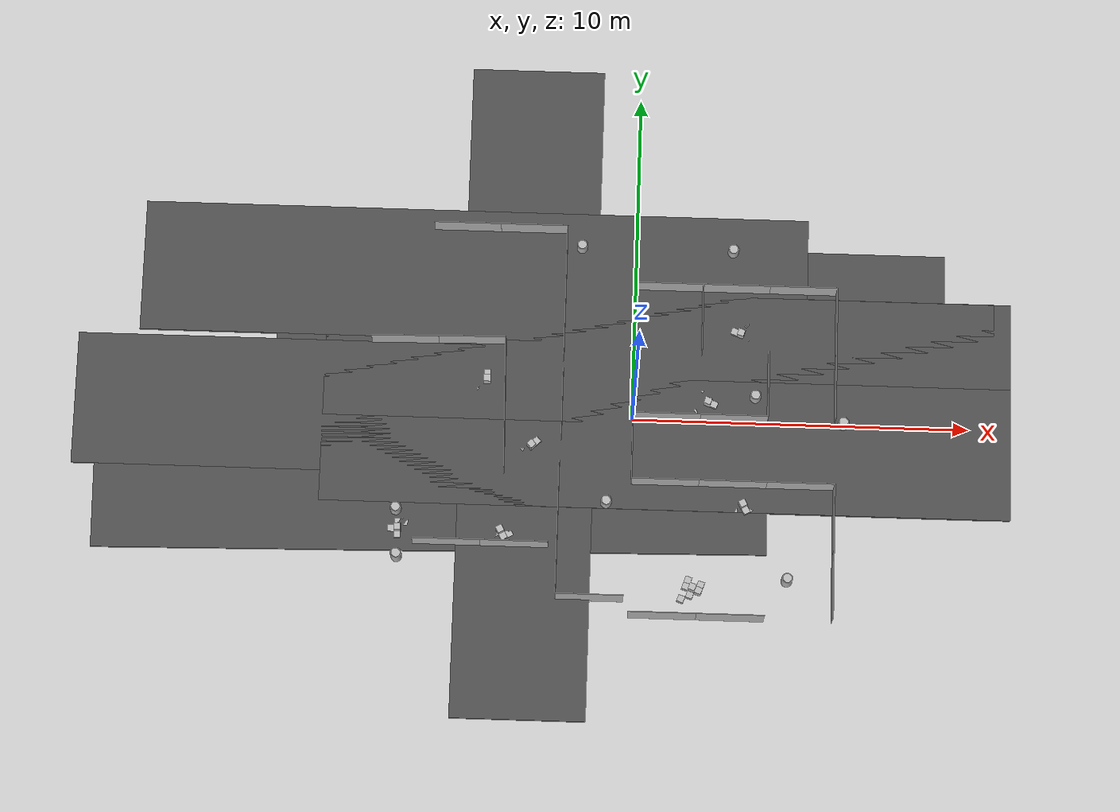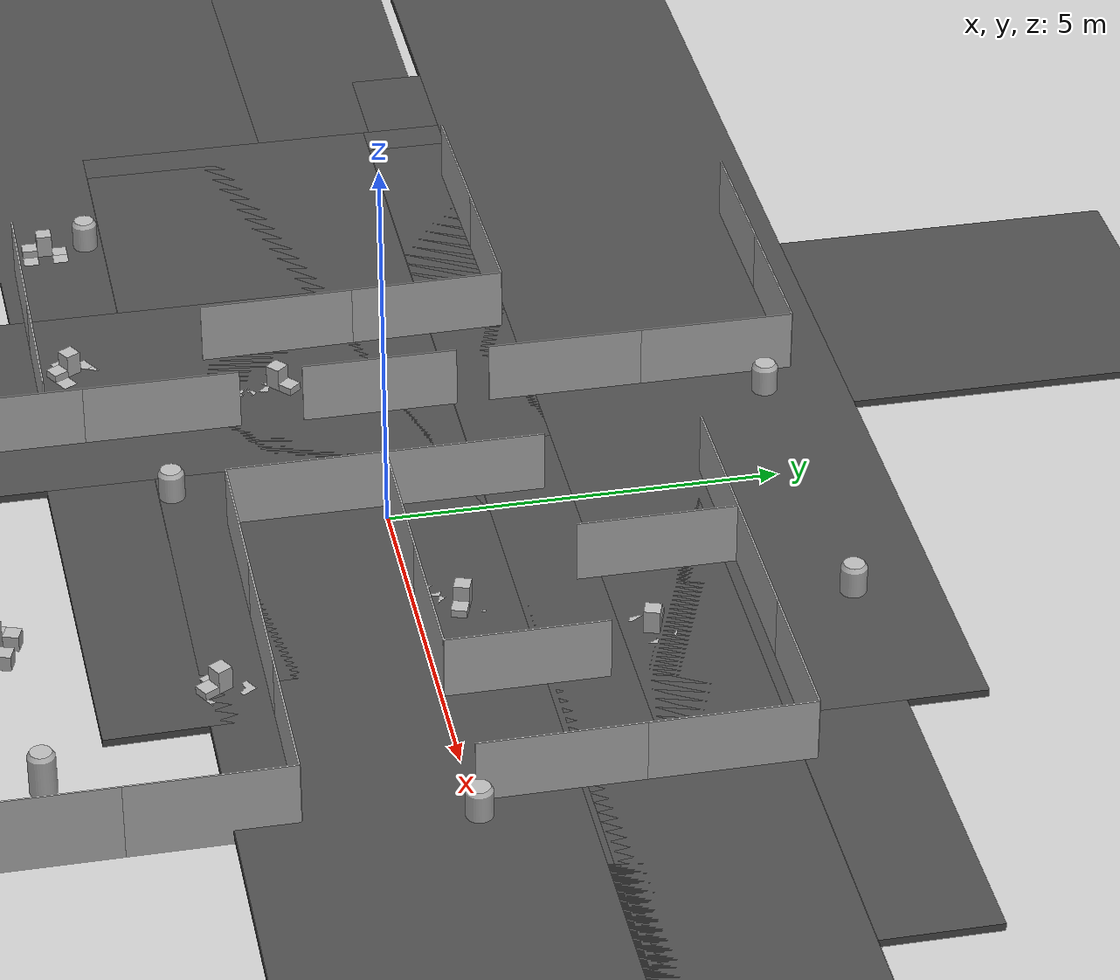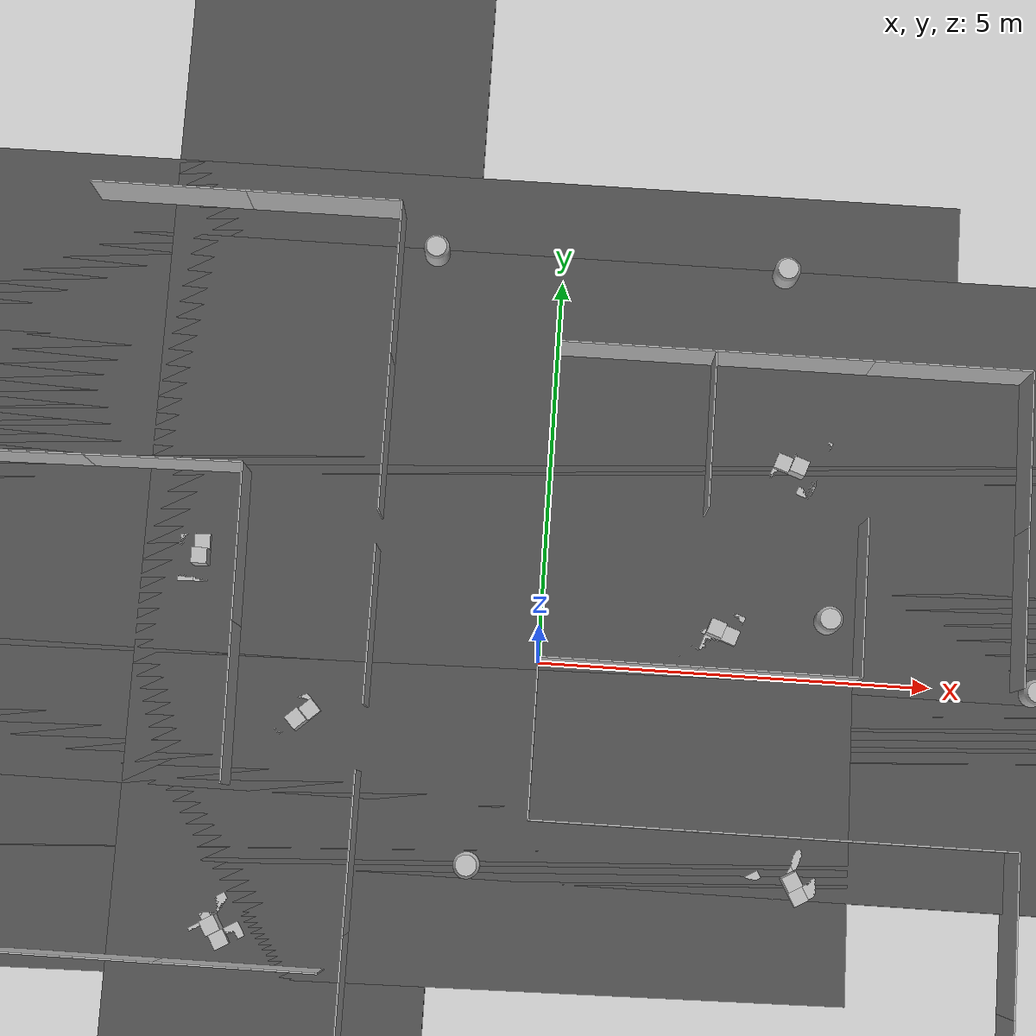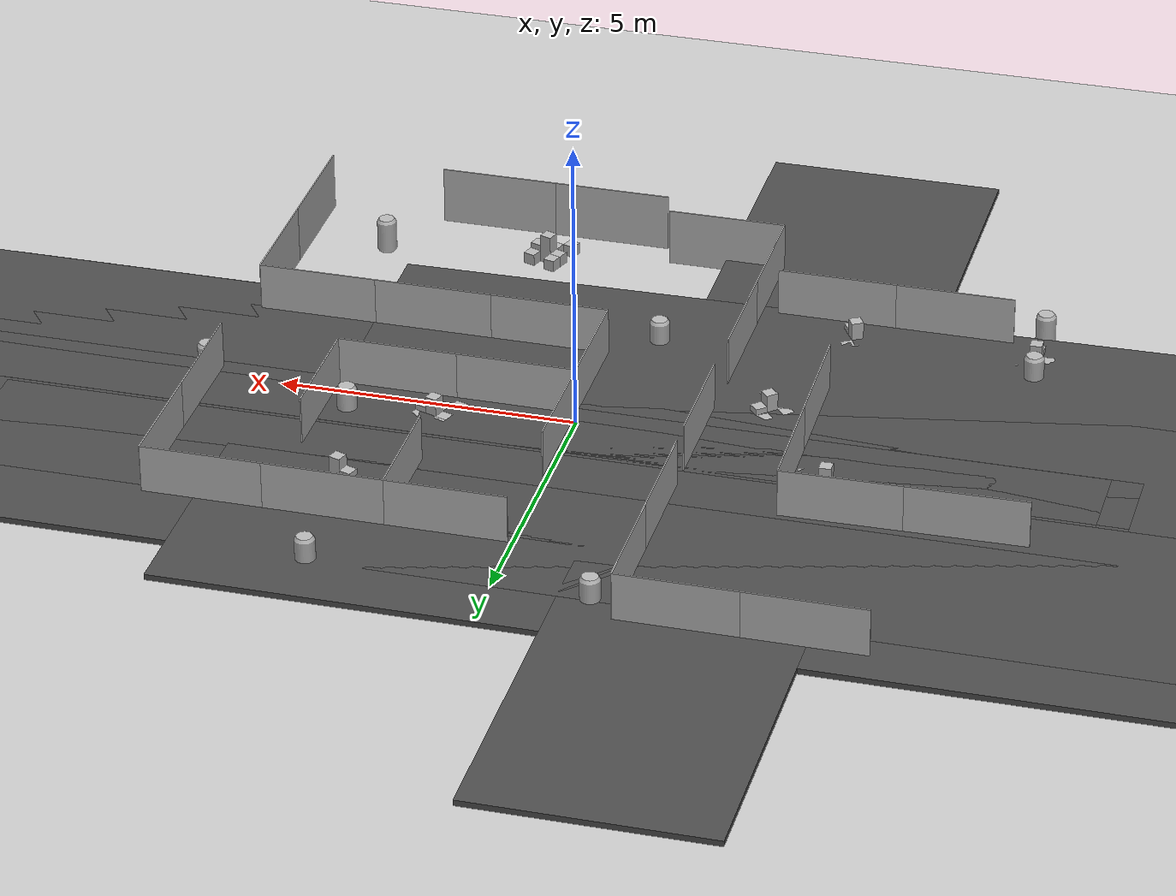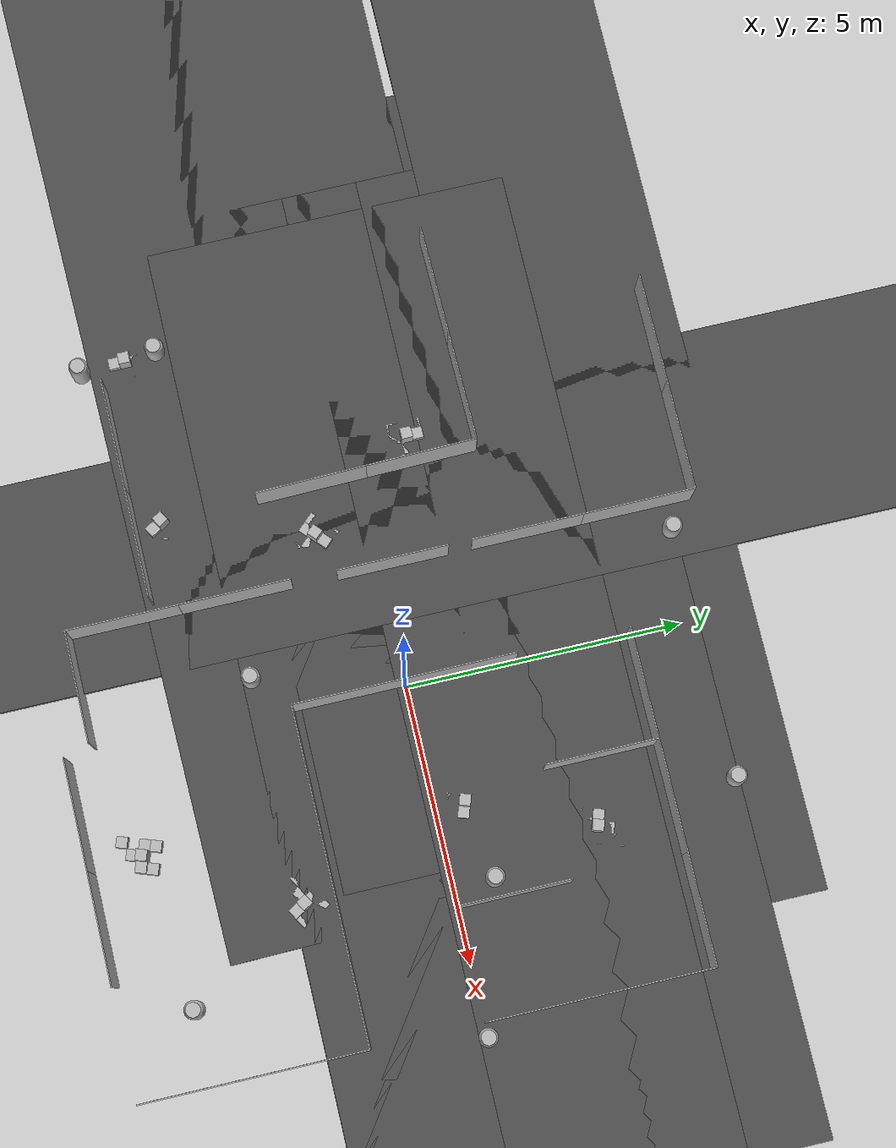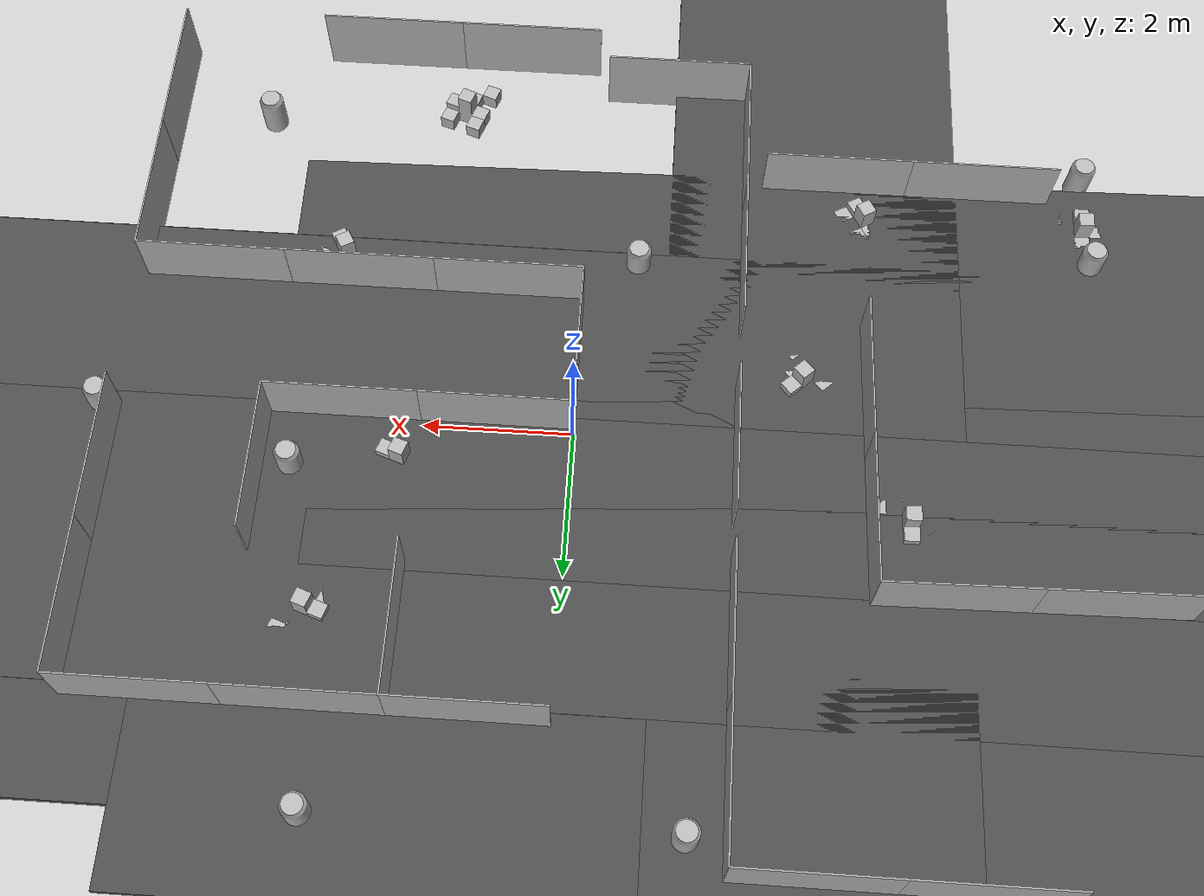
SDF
<sdf version="1.4">
  <!--Generated by blend2world.py-->
  <world name="arena_HKT_9">
    <scene>
      <ambient>0.5 0.5 0.5 1</ambient>
      <background>0.5 0.5 0.5 1</background>
      <shadows>false</shadows>
    </scene>
    <physics type="ode">
      <gravity>0 0 -9.81</gravity>
      <ode>
        <solver>
          <type>quick</type>
          <iters>1000</iters>
          <sor>1.3</sor>
        </solver>
        <constraints>
          <cfm>0.0</cfm>
          <erp>0.2</erp>
          <contact_max_correcting_vel>100.0</contact_max_correcting_vel>
          <contact_surface_layer>0.001</contact_surface_layer>
        </constraints>
      </ode>
      <real_time_update_rate>120</real_time_update_rate>
      <real_time_factor>1</real_time_factor>
      <max_step_size>0.008333</max_step_size>
    </physics>
    <light name="directional_light_1" type="directional">
      <cast_shadows>false</cast_shadows>
      <pose>0 0 30 0.1 0.1 0</pose>
      <diffuse>1.0 1.0 1.0 1</diffuse>
      <specular>.1 .1 .1 1</specular>
      <attenuation>
        <range>300</range>
      </attenuation>
      <direction>0.1 0.1 -1</direction>
    </light>
    <include>
      <uri>model://ground_plane</uri>
    </include>
    <light name="directional_light.-10.0_-12.0" type="sun">
      <pose>-10.0 -12.0 8  0 0 0</pose>
      <cast_shadows>1</cast_shadows>
      <diffuse>0.5 0.5 0.5 1</diffuse>
      <specular>0.1 0.1 0.1 1</specular>
      <attenuation>
        <range>20</range>
        <constant>0.5</constant>
        <linear>0.01</linear>
        <quadratic>0.00</quadratic>
      </attenuation>
      <direction>0.1 0.1 -1.0</direction>
    </light>
    <light name="directional_light.-10.0_0.0" type="sun">
      <pose>-10.0 0.0 8  0 0 0</pose>
      <cast_shadows>1</cast_shadows>
      <diffuse>0.5 0.5 0.5 1</diffuse>
      <specular>0.1 0.1 0.1 1</specular>
      <attenuation>
        <range>20</range>
        <constant>0.5</constant>
        <linear>0.01</linear>
        <quadratic>0.00</quadratic>
      </attenuation>
      <direction>0.1 0.1 -1.0</direction>
    </light>
    <light name="directional_light.-10.0_12.0" type="sun">
      <pose>-10.0 12.0 8  0 0 0</pose>
      <cast_shadows>1</cast_shadows>
      <diffuse>0.5 0.5 0.5 1</diffuse>
      <specular>0.1 0.1 0.1 1</specular>
      <attenuation>
        <range>20</range>
        <constant>0.5</constant>
        <linear>0.01</linear>
        <quadratic>0.00</quadratic>
      </attenuation>
      <direction>0.1 0.1 -1.0</direction>
    </light>
    <light name="directional_light.0.0_-12.0" type="sun">
      <pose>0.0 -12.0 8  0 0 0</pose>
      <cast_shadows>1</cast_shadows>
      <diffuse>0.5 0.5 0.5 1</diffuse>
      <specular>0.1 0.1 0.1 1</specular>
      <attenuation>
        <range>20</range>
        <constant>0.5</constant>
        <linear>0.01</linear>
        <quadratic>0.00</quadratic>
      </attenuation>
      <direction>0.1 0.1 -1.0</direction>
    </light>
    <light name="directional_light.0.0_0.0" type="sun">
      <pose>0.0 0.0 8  0 0 0</pose>
      <cast_shadows>1</cast_shadows>
      <diffuse>0.5 0.5 0.5 1</diffuse>
      <specular>0.1 0.1 0.1 1</specular>
      <attenuation>
        <range>20</range>
        <constant>0.5</constant>
        <linear>0.01</linear>
        <quadratic>0.00</quadratic>
      </attenuation>
      <direction>0.1 0.1 -1.0</direction>
    </light>
    <light name="directional_light.0.0_12.0" type="sun">
      <pose>0.0 12.0 8  0 0 0</pose>
      <cast_shadows>1</cast_shadows>
      <diffuse>0.5 0.5 0.5 1</diffuse>
      <specular>0.1 0.1 0.1 1</specular>
      <attenuation>
        <range>20</range>
        <constant>0.5</constant>
        <linear>0.01</linear>
        <quadratic>0.00</quadratic>
      </attenuation>
      <direction>0.1 0.1 -1.0</direction>
    </light>
    <light name="directional_light.10.0_-12.0" type="sun">
      <pose>10.0 -12.0 8  0 0 0</pose>
      <cast_shadows>1</cast_shadows>
      <diffuse>0.5 0.5 0.5 1</diffuse>
      <specular>0.1 0.1 0.1 1</specular>
      <attenuation>
        <range>20</range>
        <constant>0.5</constant>
        <linear>0.01</linear>
        <quadratic>0.00</quadratic>
      </attenuation>
      <direction>0.1 0.1 -1.0</direction>
    </light>
    <light name="directional_light.10.0_0.0" type="sun">
      <pose>10.0 0.0 8  0 0 0</pose>
      <cast_shadows>1</cast_shadows>
      <diffuse>0.5 0.5 0.5 1</diffuse>
      <specular>0.1 0.1 0.1 1</specular>
      <attenuation>
        <range>20</range>
        <constant>0.5</constant>
        <linear>0.01</linear>
        <quadratic>0.00</quadratic>
      </attenuation>
      <direction>0.1 0.1 -1.0</direction>
    </light>
    <light name="directional_light.10.0_12.0" type="sun">
      <pose>10.0 12.0 8  0 0 0</pose>
      <cast_shadows>1</cast_shadows>
      <diffuse>0.5 0.5 0.5 1</diffuse>
      <specular>0.1 0.1 0.1 1</specular>
      <attenuation>
        <range>20</range>
        <constant>0.5</constant>
        <linear>0.01</linear>
        <quadratic>0.00</quadratic>
      </attenuation>
      <direction>0.1 0.1 -1.0</direction>
    </light>
    <include>
      <name>barrel_110l.064</name>
      <pose>-6.941155910491943 -2.995645046234131 0.0  0.0 0.0 0.0</pose>
      <uri>model://barrel_110l</uri>
    </include>
    <include>
      <name>barrel_110l.065</name>
      <pose>-1.6601641178131104 5.237995624542236 0.0  0.0 0.0 0.0</pose>
      <uri>model://barrel_110l</uri>
    </include>
    <include>
      <name>barrel_110l.066</name>
      <pose>2.890841007232666 5.237995624542236 0.0  0.0 0.0 0.0</pose>
      <uri>model://barrel_110l</uri>
    </include>
    <include>
      <name>barrel_110l.067</name>
      <pose>4.665648460388184 -4.783429145812988 0.0  0.0 0.0 0.0</pose>
      <uri>model://barrel_110l</uri>
    </include>
    <include>
      <name>barrel_110l.068</name>
      <pose>-6.876338481903076 -4.385210990905762 0.0  0.0 0.0 0.0</pose>
      <uri>model://barrel_110l</uri>
    </include>
    <include>
      <name>barrel_110l.069</name>
      <pose>6.263016223907471 -0.004051387310028076 0.0  0.0 0.0 0.0</pose>
      <uri>model://barrel_110l</uri>
    </include>
    <include>
      <name>barrel_110l.070</name>
      <pose>3.6342127323150635 0.7459036111831665 0.0  0.0 0.0 0.0</pose>
      <uri>model://barrel_110l</uri>
    </include>
    <include>
      <name>barrel_110l.071</name>
      <pose>-0.7261247634887695 -2.6033458709716797 0.0  0.0 0.0 0.0</pose>
      <uri>model://barrel_110l</uri>
    </include>
    <include>
      <name>cube_20x20.1075</name>
      <pose>-4.375776290893555 0.8407224416732788 0.10000000149011612  0.0 -0.0 6.301559925079346</pose>
      <uri>model://cube_20x20</uri>
    </include>
    <include>
      <name>cube_20x20.1076</name>
      <pose>-4.179484844207764 1.044363260269165 0.10000000149011612  0.0 -0.0 6.301559925079346</pose>
      <uri>model://cube_20x20</uri>
    </include>
    <include>
      <name>cube_20x20.1077</name>
      <pose>-3.975843906402588 0.8480718731880188 0.10000000149011612  0.0 -0.0 6.301559925079346</pose>
      <uri>model://cube_20x20</uri>
    </include>
    <include>
      <name>cube_20x20.1078</name>
      <pose>-4.575742721557617 0.8370477557182312 0.10000000149011612  0.0 -0.0 6.301559925079346</pose>
      <uri>model://cube_20x20</uri>
    </include>
    <include>
      <name>cube_20x20.1079</name>
      <pose>-4.583092212677002 1.2369798421859741 0.10000000149011612  0.0 -0.0 6.301559925079346</pose>
      <uri>model://cube_20x20</uri>
    </include>
    <include>
      <name>cube_20x20.1080</name>
      <pose>-4.375776290893555 0.8407224416732788 0.10000000149011612  0.0 -0.0 6.301559925079346</pose>
      <uri>model://cube_20x20</uri>
    </include>
    <include>
      <name>cube_20x20.1081</name>
      <pose>-4.179484844207764 1.044363260269165 0.10000000149011612  0.0 -0.0 6.301559925079346</pose>
      <uri>model://cube_20x20</uri>
    </include>
    <include>
      <name>cube_20x20.1082</name>
      <pose>-3.975843906402588 0.8480718731880188 0.10000000149011612  0.0 -0.0 6.301559925079346</pose>
      <uri>model://cube_20x20</uri>
    </include>
    <include>
      <name>cube_20x20.1083</name>
      <pose>-4.575742721557617 0.8370477557182312 0.10000000149011612  0.0 -0.0 6.301559925079346</pose>
      <uri>model://cube_20x20</uri>
    </include>
    <include>
      <name>cube_20x20.1084</name>
      <pose>-4.583092212677002 1.2369798421859741 0.10000000149011612  0.0 -0.0 6.301559925079346</pose>
      <uri>model://cube_20x20</uri>
    </include>
    <include>
      <name>cube_20x20.1085</name>
      <pose>-6.874878406524658 -3.3630831241607666 0.10000000149011612  0.0 -0.0 3.141592502593994</pose>
      <uri>model://cube_20x20</uri>
    </include>
    <include>
      <name>cube_20x20.1086</name>
      <pose>-7.074878215789795 -3.5630829334259033 0.10000000149011612  0.0 -0.0 3.141592502593994</pose>
      <uri>model://cube_20x20</uri>
    </include>
    <include>
      <name>cube_20x20.1087</name>
      <pose>-6.674878120422363 -3.3630831241607666 0.10000000149011612  0.0 -0.0 3.141592502593994</pose>
      <uri>model://cube_20x20</uri>
    </include>
    <include>
      <name>cube_20x20.1088</name>
      <pose>-6.674878120422363 -3.76308274269104 0.10000000149011612  0.0 -0.0 3.141592502593994</pose>
      <uri>model://cube_20x20</uri>
    </include>
    <include>
      <name>cube_20x20.1089</name>
      <pose>-6.874878406524658 -3.3630831241607666 0.10000000149011612  0.0 -0.0 3.141592502593994</pose>
      <uri>model://cube_20x20</uri>
    </include>
    <include>
      <name>cube_20x20.1090</name>
      <pose>-7.074878215789795 -3.5630829334259033 0.10000000149011612  0.0 -0.0 3.141592502593994</pose>
      <uri>model://cube_20x20</uri>
    </include>
    <include>
      <name>cube_20x20.1091</name>
      <pose>-6.674878120422363 -3.3630831241607666 0.10000000149011612  0.0 -0.0 3.141592502593994</pose>
      <uri>model://cube_20x20</uri>
    </include>
    <include>
      <name>cube_20x20.1092</name>
      <pose>-6.674878120422363 -3.76308274269104 0.10000000149011612  0.0 -0.0 3.141592502593994</pose>
      <uri>model://cube_20x20</uri>
    </include>
    <include>
      <name>cube_20x20.1093</name>
      <pose>-3.9385533332824707 -3.3717634677886963 0.10000000149011612  0.0 -0.0 3.6651763916015625</pose>
      <uri>model://cube_20x20</uri>
    </include>
    <include>
      <name>cube_20x20.1094</name>
      <pose>-4.011762619018555 -3.6449673175811768 0.10000000149011612  0.0 -0.0 3.6651763916015625</pose>
      <uri>model://cube_20x20</uri>
    </include>
    <include>
      <name>cube_20x20.1095</name>
      <pose>-3.7653465270996094 -3.271765947341919 0.10000000149011612  0.0 -0.0 3.6651763916015625</pose>
      <uri>model://cube_20x20</uri>
    </include>
    <include>
      <name>cube_20x20.1096</name>
      <pose>-3.565351963043213 -3.6181790828704834 0.10000000149011612  0.0 -0.0 3.6651763916015625</pose>
      <uri>model://cube_20x20</uri>
    </include>
    <include>
      <name>cube_20x20.1097</name>
      <pose>-3.9385533332824707 -3.3717634677886963 0.10000000149011612  0.0 -0.0 3.6651763916015625</pose>
      <uri>model://cube_20x20</uri>
    </include>
    <include>
      <name>cube_20x20.1098</name>
      <pose>-4.011762619018555 -3.6449673175811768 0.10000000149011612  0.0 -0.0 3.6651763916015625</pose>
      <uri>model://cube_20x20</uri>
    </include>
    <include>
      <name>cube_20x20.1099</name>
      <pose>-3.7653465270996094 -3.271765947341919 0.10000000149011612  0.0 -0.0 3.6651763916015625</pose>
      <uri>model://cube_20x20</uri>
    </include>
    <include>
      <name>cube_20x20.1100</name>
      <pose>-3.565351963043213 -3.6181790828704834 0.10000000149011612  0.0 -0.0 3.6651763916015625</pose>
      <uri>model://cube_20x20</uri>
    </include>
    <include>
      <name>cube_20x20.1101</name>
      <pose>-3.1368727684020996 -1.071094274520874 0.10000000149011612  0.0 0.0 5.4528021812438965</pose>
      <uri>model://cube_20x20</uri>
    </include>
    <include>
      <name>cube_20x20.1102</name>
      <pose>-2.8543167114257812 -1.0838134288787842 0.10000000149011612  0.0 0.0 5.4528021812438965</pose>
      <uri>model://cube_20x20</uri>
    </include>
    <include>
      <name>cube_20x20.1103</name>
      <pose>-2.8670363426208496 -1.3663697242736816 0.10000000149011612  0.0 0.0 5.4528021812438965</pose>
      <uri>model://cube_20x20</uri>
    </include>
    <include>
      <name>cube_20x20.1104</name>
      <pose>-3.2717912197113037 -0.9234559535980225 0.10000000149011612  0.0 0.0 5.4528021812438965</pose>
      <uri>model://cube_20x20</uri>
    </include>
    <include>
      <name>cube_20x20.1105</name>
      <pose>-2.976515293121338 -0.6536192893981934 0.10000000149011612  0.0 0.0 5.4528021812438965</pose>
      <uri>model://cube_20x20</uri>
    </include>
    <include>
      <name>cube_20x20.1106</name>
      <pose>-3.1368727684020996 -1.071094274520874 0.10000000149011612  0.0 0.0 5.4528021812438965</pose>
      <uri>model://cube_20x20</uri>
    </include>
    <include>
      <name>cube_20x20.1107</name>
      <pose>-2.8543167114257812 -1.0838134288787842 0.10000000149011612  0.0 0.0 5.4528021812438965</pose>
      <uri>model://cube_20x20</uri>
    </include>
    <include>
      <name>cube_20x20.1108</name>
      <pose>-2.8670363426208496 -1.3663697242736816 0.10000000149011612  0.0 0.0 5.4528021812438965</pose>
      <uri>model://cube_20x20</uri>
    </include>
    <include>
      <name>cube_20x20.1109</name>
      <pose>-3.2717912197113037 -0.9234559535980225 0.10000000149011612  0.0 0.0 5.4528021812438965</pose>
      <uri>model://cube_20x20</uri>
    </include>
    <include>
      <name>cube_20x20.1110</name>
      <pose>-2.976515293121338 -0.6536192893981934 0.10000000149011612  0.0 0.0 5.4528021812438965</pose>
      <uri>model://cube_20x20</uri>
    </include>
    <include>
      <name>cube_20x30.184</name>
      <pose>-4.383125305175781 1.2406545877456665 0.15000000596046448  0.0 -0.0 6.301559925079346</pose>
      <uri>model://cube_20x30</uri>
    </include>
    <include>
      <name>cube_20x30.185</name>
      <pose>-4.383125305175781 1.2406545877456665 0.15000000596046448  0.0 -0.0 6.301559925079346</pose>
      <uri>model://cube_20x30</uri>
    </include>
    <include>
      <name>cube_20x30.186</name>
      <pose>-6.874878406524658 -3.76308274269104 0.15000000596046448  0.0 -0.0 3.141592502593994</pose>
      <uri>model://cube_20x30</uri>
    </include>
    <include>
      <name>cube_20x30.187</name>
      <pose>-6.874878406524658 -3.76308274269104 0.15000000596046448  0.0 -0.0 3.141592502593994</pose>
      <uri>model://cube_20x30</uri>
    </include>
    <include>
      <name>cube_20x30.188</name>
      <pose>-3.738558769226074 -3.7181766033172607 0.15000000596046448  0.0 -0.0 3.6651763916015625</pose>
      <uri>model://cube_20x30</uri>
    </include>
    <include>
      <name>cube_20x30.189</name>
      <pose>-3.738558769226074 -3.7181766033172607 0.15000000596046448  0.0 -0.0 3.6651763916015625</pose>
      <uri>model://cube_20x30</uri>
    </include>
    <include>
      <name>cube_20x30.190</name>
      <pose>-2.841596841812134 -0.8012573719024658 0.15000000596046448  0.0 0.0 5.4528021812438965</pose>
      <uri>model://cube_20x30</uri>
    </include>
    <include>
      <name>cube_20x30.191</name>
      <pose>-2.841596841812134 -0.8012573719024658 0.15000000596046448  0.0 0.0 5.4528021812438965</pose>
      <uri>model://cube_20x30</uri>
    </include>
    <include>
      <name>cube_20x50.178</name>
      <pose>-4.379450798034668 1.0406885147094727 0.25  0.0 -0.0 6.301559925079346</pose>
      <uri>model://cube_20x50</uri>
    </include>
    <include>
      <name>cube_20x50.179</name>
      <pose>-4.379450798034668 1.0406885147094727 0.25  0.0 -0.0 6.301559925079346</pose>
      <uri>model://cube_20x50</uri>
    </include>
    <include>
      <name>cube_20x50.180</name>
      <pose>-6.874878406524658 -3.5630829334259033 0.25  0.0 -0.0 3.141592502593994</pose>
      <uri>model://cube_20x50</uri>
    </include>
    <include>
      <name>cube_20x50.181</name>
      <pose>-6.874878406524658 -3.5630829334259033 0.25  0.0 -0.0 3.141592502593994</pose>
      <uri>model://cube_20x50</uri>
    </include>
    <include>
      <name>cube_20x50.182</name>
      <pose>-3.8385560512542725 -3.5449702739715576 0.25  0.0 -0.0 3.6651763916015625</pose>
      <uri>model://cube_20x50</uri>
    </include>
    <include>
      <name>cube_20x50.183</name>
      <pose>-3.8385560512542725 -3.5449702739715576 0.25  0.0 -0.0 3.6651763916015625</pose>
      <uri>model://cube_20x50</uri>
    </include>
    <include>
      <name>cube_20x50.184</name>
      <pose>-2.989234209060669 -0.9361758232116699 0.25  0.0 0.0 5.4528021812438965</pose>
      <uri>model://cube_20x50</uri>
    </include>
    <include>
      <name>cube_20x50.185</name>
      <pose>-2.989234209060669 -0.9361758232116699 0.25  0.0 0.0 5.4528021812438965</pose>
      <uri>model://cube_20x50</uri>
    </include>
    <include>
      <name>ramp.079</name>
      <pose>-3.1412580013275146 0.8252742290496826 0.15000000596046448  0.0 -0.0 7.853981971740723</pose>
      <uri>model://ramp</uri>
    </include>
    <include>
      <name>ramp.080</name>
      <pose>-5.96612548828125 -2.2167935371398926 0.15000000596046448  0.0 -0.0 9.44315242767334</pose>
      <uri>model://ramp</uri>
    </include>
    <include>
      <name>ramp.081</name>
      <pose>-6.66489315032959 0.13354206085205078 0.15000000596046448  0.0 -0.0 6.283185005187988</pose>
      <uri>model://ramp</uri>
    </include>
    <include>
      <name>ramp.082</name>
      <pose>-4.8568115234375 4.303653717041016 0.15000000596046448  0.0 -0.0 6.283185005187988</pose>
      <uri>model://ramp</uri>
    </include>
    <include>
      <name>wall_2x1.415</name>
      <pose>-3.801290512084961 -0.8092706203460693 0.5130000114440918  0.0 -0.0 4.7307634353637695</pose>
      <uri>model://wall_2x1</uri>
    </include>
    <include>
      <name>wall_2x1.416</name>
      <pose>-6.855904579162598 2.1351027488708496 0.5130000114440918  0.0 -0.0 3.1599674224853516</pose>
      <uri>model://wall_2x1</uri>
    </include>
    <include>
      <name>wall_stand.929</name>
      <pose>-1.8005000352859497 2.0 0.03449999913573265  0.0 -0.0 1.570796251296997</pose>
      <uri>model://wall_stand</uri>
    </include>
    <include>
      <name>wall_stand.930</name>
      <pose>-0.19949999451637268 2.0 0.03449999913573265  0.0 -0.0 1.570796251296997</pose>
      <uri>model://wall_stand</uri>
    </include>
    <include>
      <name>wall_2x1.417</name>
      <pose>-3.8380374908447266 1.1903918981552124 0.5130000114440918  0.0 -0.0 4.7307634353637695</pose>
      <uri>model://wall_2x1</uri>
    </include>
    <include>
      <name>wall_2x1.418</name>
      <pose>-4.8562421798706055 2.1718497276306152 0.5130000114440918  0.0 -0.0 3.1599674224853516</pose>
      <uri>model://wall_2x1</uri>
    </include>
    <include>
      <name>wall_stand.931</name>
      <pose>-0.19949999451637268 2.0 0.03449999913573265  0.0 -0.0 1.570796251296997</pose>
      <uri>model://wall_stand</uri>
    </include>
    <include>
      <name>wall_2x1.419</name>
      <pose>-2.147331953048706 -2.5302858352661133 0.5130000114440918  0.0 -0.0 1.570796251296997</pose>
      <uri>model://wall_2x1</uri>
    </include>
    <include>
      <name>wall_stand.932</name>
      <pose>-1.8005000352859497 2.0 0.03449999913573265  0.0 -0.0 1.570796251296997</pose>
      <uri>model://wall_stand</uri>
    </include>
    <include>
      <name>wall_stand.933</name>
      <pose>-0.19949999451637268 2.0 0.03449999913573265  0.0 -0.0 1.570796251296997</pose>
      <uri>model://wall_stand</uri>
    </include>
    <include>
      <name>wall_2x1.420</name>
      <pose>-1.1473321914672852 -5.530285835266113 0.5130000114440918  0.0 -0.0 3.141592502593994</pose>
      <uri>model://wall_2x1</uri>
    </include>
    <include>
      <name>wall_2x1.421</name>
      <pose>-2.147332191467285 -4.530285835266113 0.5130000114440918  0.0 -0.0 1.570796251296997</pose>
      <uri>model://wall_2x1</uri>
    </include>
    <include>
      <name>wall_stand.934</name>
      <pose>-0.19949999451637268 2.0 0.03449999913573265  0.0 -0.0 1.570796251296997</pose>
      <uri>model://wall_stand</uri>
    </include>
    <include>
      <name>wall_2x1.422</name>
      <pose>-2.1166141033172607 2.695002794265747 0.5130000114440918  0.0 -0.0 4.71238899230957</pose>
      <uri>model://wall_2x1</uri>
    </include>
    <include>
      <name>wall_stand.935</name>
      <pose>-1.8005000352859497 2.0 0.03449999913573265  0.0 -0.0 1.570796251296997</pose>
      <uri>model://wall_stand</uri>
    </include>
    <include>
      <name>wall_stand.936</name>
      <pose>-0.19949999451637268 2.0 0.03449999913573265  0.0 -0.0 1.570796251296997</pose>
      <uri>model://wall_stand</uri>
    </include>
    <include>
      <name>wall_2x1.423</name>
      <pose>-5.116613388061523 5.695002555847168 0.5130000114440918  0.0 -0.0 6.283185005187988</pose>
      <uri>model://wall_2x1</uri>
    </include>
    <include>
      <name>wall_2x1.424</name>
      <pose>-3.1166136264801025 5.695002555847168 0.5130000114440918  0.0 -0.0 6.283185005187988</pose>
      <uri>model://wall_2x1</uri>
    </include>
    <include>
      <name>wall_2x1.425</name>
      <pose>-2.1166136264801025 4.695002555847168 0.5130000114440918  0.0 -0.0 4.71238899230957</pose>
      <uri>model://wall_2x1</uri>
    </include>
    <include>
      <name>wall_stand.937</name>
      <pose>-0.19949999451637268 2.0 0.03449999913573265  0.0 -0.0 1.570796251296997</pose>
      <uri>model://wall_stand</uri>
    </include>
    <include>
      <name>wall_2x1.426</name>
      <pose>-2.1166141033172607 0.2739219665527344 0.5130000114440918  0.0 -0.0 4.71238899230957</pose>
      <uri>model://wall_2x1</uri>
    </include>
    <include>
      <name>wall_stand.938</name>
      <pose>-1.8005000352859497 2.0 0.03449999913573265  0.0 -0.0 1.570796251296997</pose>
      <uri>model://wall_stand</uri>
    </include>
    <include>
      <name>wall_stand.939</name>
      <pose>-0.19949999451637268 2.0 0.03449999913573265  0.0 -0.0 1.570796251296997</pose>
      <uri>model://wall_stand</uri>
    </include>
    <include>
      <name>wall_stand.940</name>
      <pose>-3.7865824699401855 -1.609635353088379 0.03450000286102295  0.0 -0.0 3.1599674224853516</pose>
      <uri>model://wall_stand</uri>
    </include>
    <include>
      <name>wall_stand.941</name>
      <pose>-3.815998077392578 -0.008905649185180664 0.03450000286102295  0.0 -0.0 3.1599674224853516</pose>
      <uri>model://wall_stand</uri>
    </include>
    <include>
      <name>wall_stand.942</name>
      <pose>-3.823329448699951 0.39002686738967896 0.03450000286102295  0.0 -0.0 3.1599674224853516</pose>
      <uri>model://wall_stand</uri>
    </include>
    <include>
      <name>wall_stand.943</name>
      <pose>-3.8527450561523438 1.9907567501068115 0.03450000286102295  0.0 -0.0 3.1599674224853516</pose>
      <uri>model://wall_stand</uri>
    </include>
    <include>
      <name>wall_stand.944</name>
      <pose>-2.346832275390625 -5.530285835266113 0.03450000286102295  0.0 -0.0 1.570796251296997</pose>
      <uri>model://wall_stand</uri>
    </include>
    <include>
      <name>wall_stand.945</name>
      <pose>-5.917113304138184 5.695002555847168 0.03450000286102295  0.0 -0.0 4.71238899230957</pose>
      <uri>model://wall_stand</uri>
    </include>
    <include>
      <name>wall_stand.946</name>
      <pose>-4.316113471984863 5.695002555847168 0.03450000286102295  0.0 -0.0 4.71238899230957</pose>
      <uri>model://wall_stand</uri>
    </include>
    <include>
      <name>wall_stand.947</name>
      <pose>-2.316113233566284 5.695002555847168 0.03450000286102295  0.0 -0.0 4.71238899230957</pose>
      <uri>model://wall_stand</uri>
    </include>
    <include>
      <name>wall_stand.948</name>
      <pose>-3.9171135425567627 5.695002555847168 0.03450000286102295  0.0 -0.0 4.71238899230957</pose>
      <uri>model://wall_stand</uri>
    </include>
    <include>
      <name>cube_20x20.1111</name>
      <pose>2.0343916416168213 0.613365888595581 0.10000000149011612  0.0 0.0 4.376082897186279</pose>
      <uri>model://cube_20x20</uri>
    </include>
    <include>
      <name>cube_20x20.1112</name>
      <pose>2.1571874618530273 0.358569860458374 0.10000000149011612  0.0 0.0 4.376082897186279</pose>
      <uri>model://cube_20x20</uri>
    </include>
    <include>
      <name>cube_20x20.1113</name>
      <pose>1.902390956878662 0.23577475547790527 0.10000000149011612  0.0 0.0 4.376082897186279</pose>
      <uri>model://cube_20x20</uri>
    </include>
    <include>
      <name>cube_20x20.1114</name>
      <pose>2.1003925800323486 0.8021619319915771 0.10000000149011612  0.0 0.0 4.376082897186279</pose>
      <uri>model://cube_20x20</uri>
    </include>
    <include>
      <name>cube_20x20.1115</name>
      <pose>2.4779841899871826 0.6701610088348389 0.10000000149011612  0.0 0.0 4.376082897186279</pose>
      <uri>model://cube_20x20</uri>
    </include>
    <include>
      <name>cube_20x20.1116</name>
      <pose>2.0343916416168213 0.613365888595581 0.10000000149011612  0.0 0.0 4.376082897186279</pose>
      <uri>model://cube_20x20</uri>
    </include>
    <include>
      <name>cube_20x20.1117</name>
      <pose>2.1571874618530273 0.358569860458374 0.10000000149011612  0.0 0.0 4.376082897186279</pose>
      <uri>model://cube_20x20</uri>
    </include>
    <include>
      <name>cube_20x20.1118</name>
      <pose>1.902390956878662 0.23577475547790527 0.10000000149011612  0.0 0.0 4.376082897186279</pose>
      <uri>model://cube_20x20</uri>
    </include>
    <include>
      <name>cube_20x20.1119</name>
      <pose>2.1003925800323486 0.8021619319915771 0.10000000149011612  0.0 0.0 4.376082897186279</pose>
      <uri>model://cube_20x20</uri>
    </include>
    <include>
      <name>cube_20x20.1120</name>
      <pose>2.4779841899871826 0.6701610088348389 0.10000000149011612  0.0 0.0 4.376082897186279</pose>
      <uri>model://cube_20x20</uri>
    </include>
    <include>
      <name>cube_20x20.1121</name>
      <pose>3.3604865074157715 2.6194584369659424 0.10000000149011612  0.0 0.0 7.517675399780273</pose>
      <uri>model://cube_20x20</uri>
    </include>
    <include>
      <name>cube_20x20.1122</name>
      <pose>3.2376906871795654 2.8742544651031494 0.10000000149011612  0.0 0.0 7.517675399780273</pose>
      <uri>model://cube_20x20</uri>
    </include>
    <include>
      <name>cube_20x20.1123</name>
      <pose>3.4924871921539307 2.9970500469207764 0.10000000149011612  0.0 0.0 7.517675399780273</pose>
      <uri>model://cube_20x20</uri>
    </include>
    <include>
      <name>cube_20x20.1124</name>
      <pose>3.294485569000244 2.4306623935699463 0.10000000149011612  0.0 0.0 7.517675399780273</pose>
      <uri>model://cube_20x20</uri>
    </include>
    <include>
      <name>cube_20x20.1125</name>
      <pose>2.91689395904541 2.5626633167266846 0.10000000149011612  0.0 0.0 7.517675399780273</pose>
      <uri>model://cube_20x20</uri>
    </include>
    <include>
      <name>cube_20x20.1126</name>
      <pose>3.3604865074157715 2.6194584369659424 0.10000000149011612  0.0 0.0 7.517675399780273</pose>
      <uri>model://cube_20x20</uri>
    </include>
    <include>
      <name>cube_20x20.1127</name>
      <pose>3.2376906871795654 2.8742544651031494 0.10000000149011612  0.0 0.0 7.517675399780273</pose>
      <uri>model://cube_20x20</uri>
    </include>
    <include>
      <name>cube_20x20.1128</name>
      <pose>3.4924871921539307 2.9970500469207764 0.10000000149011612  0.0 0.0 7.517675399780273</pose>
      <uri>model://cube_20x20</uri>
    </include>
    <include>
      <name>cube_20x20.1129</name>
      <pose>3.294485569000244 2.4306623935699463 0.10000000149011612  0.0 0.0 7.517675399780273</pose>
      <uri>model://cube_20x20</uri>
    </include>
    <include>
      <name>cube_20x20.1130</name>
      <pose>2.91689395904541 2.5626633167266846 0.10000000149011612  0.0 0.0 7.517675399780273</pose>
      <uri>model://cube_20x20</uri>
    </include>
    <include>
      <name>cube_20x20.1131</name>
      <pose>3.2194247245788574 -2.3717634677886963 0.10000000149011612  0.0 -0.0 3.6651763916015625</pose>
      <uri>model://cube_20x20</uri>
    </include>
    <include>
      <name>cube_20x20.1132</name>
      <pose>3.1462156772613525 -2.6449673175811768 0.10000000149011612  0.0 -0.0 3.6651763916015625</pose>
      <uri>model://cube_20x20</uri>
    </include>
    <include>
      <name>cube_20x20.1133</name>
      <pose>2.873011827468872 -2.5717580318450928 0.10000000149011612  0.0 -0.0 3.6651763916015625</pose>
      <uri>model://cube_20x20</uri>
    </include>
    <include>
      <name>cube_20x20.1134</name>
      <pose>3.3926315307617188 -2.271765947341919 0.10000000149011612  0.0 -0.0 3.6651763916015625</pose>
      <uri>model://cube_20x20</uri>
    </include>
    <include>
      <name>cube_20x20.1135</name>
      <pose>3.5926260948181152 -2.6181790828704834 0.10000000149011612  0.0 -0.0 3.6651763916015625</pose>
      <uri>model://cube_20x20</uri>
    </include>
    <include>
      <name>cube_20x20.1136</name>
      <pose>3.2194247245788574 -2.3717634677886963 0.10000000149011612  0.0 -0.0 3.6651763916015625</pose>
      <uri>model://cube_20x20</uri>
    </include>
    <include>
      <name>cube_20x20.1137</name>
      <pose>3.1462156772613525 -2.6449673175811768 0.10000000149011612  0.0 -0.0 3.6651763916015625</pose>
      <uri>model://cube_20x20</uri>
    </include>
    <include>
      <name>cube_20x20.1138</name>
      <pose>2.873011827468872 -2.5717580318450928 0.10000000149011612  0.0 -0.0 3.6651763916015625</pose>
      <uri>model://cube_20x20</uri>
    </include>
    <include>
      <name>cube_20x20.1139</name>
      <pose>3.3926315307617188 -2.271765947341919 0.10000000149011612  0.0 -0.0 3.6651763916015625</pose>
      <uri>model://cube_20x20</uri>
    </include>
    <include>
      <name>cube_20x20.1140</name>
      <pose>3.5926260948181152 -2.6181790828704834 0.10000000149011612  0.0 -0.0 3.6651763916015625</pose>
      <uri>model://cube_20x20</uri>
    </include>
    <include>
      <name>cube_20x20.1141</name>
      <pose>1.691523790359497 -5.038193702697754 0.10000000149011612  0.0 0.0 4.376082897186279</pose>
      <uri>model://cube_20x20</uri>
    </include>
    <include>
      <name>cube_20x20.1142</name>
      <pose>1.8143196105957031 -5.292989730834961 0.10000000149011612  0.0 0.0 4.376082897186279</pose>
      <uri>model://cube_20x20</uri>
    </include>
    <include>
      <name>cube_20x20.1143</name>
      <pose>1.559523105621338 -5.415785789489746 0.10000000149011612  0.0 0.0 4.376082897186279</pose>
      <uri>model://cube_20x20</uri>
    </include>
    <include>
      <name>cube_20x20.1144</name>
      <pose>1.7575247287750244 -4.849397659301758 0.10000000149011612  0.0 0.0 4.376082897186279</pose>
      <uri>model://cube_20x20</uri>
    </include>
    <include>
      <name>cube_20x20.1145</name>
      <pose>2.1351163387298584 -4.981398582458496 0.10000000149011612  0.0 0.0 4.376082897186279</pose>
      <uri>model://cube_20x20</uri>
    </include>
    <include>
      <name>cube_20x20.1146</name>
      <pose>1.691523790359497 -5.038193702697754 0.10000000149011612  0.0 0.0 4.376082897186279</pose>
      <uri>model://cube_20x20</uri>
    </include>
    <include>
      <name>cube_20x20.1147</name>
      <pose>1.8143196105957031 -5.292989730834961 0.10000000149011612  0.0 0.0 4.376082897186279</pose>
      <uri>model://cube_20x20</uri>
    </include>
    <include>
      <name>cube_20x20.1148</name>
      <pose>1.559523105621338 -5.415785789489746 0.10000000149011612  0.0 0.0 4.376082897186279</pose>
      <uri>model://cube_20x20</uri>
    </include>
    <include>
      <name>cube_20x20.1149</name>
      <pose>1.7575247287750244 -4.849397659301758 0.10000000149011612  0.0 0.0 4.376082897186279</pose>
      <uri>model://cube_20x20</uri>
    </include>
    <include>
      <name>cube_20x20.1150</name>
      <pose>2.1351163387298584 -4.981398582458496 0.10000000149011612  0.0 0.0 4.376082897186279</pose>
      <uri>model://cube_20x20</uri>
    </include>
    <include>
      <name>cube_20x30.192</name>
      <pose>2.4119834899902344 0.4813649654388428 0.15000000596046448  0.0 0.0 4.376082897186279</pose>
      <uri>model://cube_20x30</uri>
    </include>
    <include>
      <name>cube_20x30.193</name>
      <pose>2.4119834899902344 0.4813649654388428 0.15000000596046448  0.0 0.0 4.376082897186279</pose>
      <uri>model://cube_20x30</uri>
    </include>
    <include>
      <name>cube_20x30.194</name>
      <pose>2.9828946590423584 2.751459836959839 0.15000000596046448  0.0 0.0 7.517675399780273</pose>
      <uri>model://cube_20x30</uri>
    </include>
    <include>
      <name>cube_20x30.195</name>
      <pose>2.9828946590423584 2.751459836959839 0.15000000596046448  0.0 0.0 7.517675399780273</pose>
      <uri>model://cube_20x30</uri>
    </include>
    <include>
      <name>cube_20x30.196</name>
      <pose>3.419419288635254 -2.7181766033172607 0.15000000596046448  0.0 -0.0 3.6651763916015625</pose>
      <uri>model://cube_20x30</uri>
    </include>
    <include>
      <name>cube_20x30.197</name>
      <pose>3.419419288635254 -2.7181766033172607 0.15000000596046448  0.0 -0.0 3.6651763916015625</pose>
      <uri>model://cube_20x30</uri>
    </include>
    <include>
      <name>cube_20x30.198</name>
      <pose>2.06911563873291 -5.170195579528809 0.15000000596046448  0.0 0.0 4.376082897186279</pose>
      <uri>model://cube_20x30</uri>
    </include>
    <include>
      <name>cube_20x30.199</name>
      <pose>2.06911563873291 -5.170195579528809 0.15000000596046448  0.0 0.0 4.376082897186279</pose>
      <uri>model://cube_20x30</uri>
    </include>
    <include>
      <name>cube_20x50.186</name>
      <pose>2.2231879234313965 0.5473649501800537 0.25  0.0 0.0 4.376082897186279</pose>
      <uri>model://cube_20x50</uri>
    </include>
    <include>
      <name>cube_20x50.187</name>
      <pose>2.2231879234313965 0.5473649501800537 0.25  0.0 0.0 4.376082897186279</pose>
      <uri>model://cube_20x50</uri>
    </include>
    <include>
      <name>cube_20x50.188</name>
      <pose>3.1716902256011963 2.6854593753814697 0.25  0.0 0.0 7.517675399780273</pose>
      <uri>model://cube_20x50</uri>
    </include>
    <include>
      <name>cube_20x50.189</name>
      <pose>3.1716902256011963 2.6854593753814697 0.25  0.0 0.0 7.517675399780273</pose>
      <uri>model://cube_20x50</uri>
    </include>
    <include>
      <name>cube_20x50.190</name>
      <pose>3.3194220066070557 -2.5449702739715576 0.25  0.0 -0.0 3.6651763916015625</pose>
      <uri>model://cube_20x50</uri>
    </include>
    <include>
      <name>cube_20x50.191</name>
      <pose>3.3194220066070557 -2.5449702739715576 0.25  0.0 -0.0 3.6651763916015625</pose>
      <uri>model://cube_20x50</uri>
    </include>
    <include>
      <name>cube_20x50.192</name>
      <pose>1.8803200721740723 -5.104194641113281 0.25  0.0 0.0 4.376082897186279</pose>
      <uri>model://cube_20x50</uri>
    </include>
    <include>
      <name>cube_20x50.193</name>
      <pose>1.8803200721740723 -5.104194641113281 0.25  0.0 0.0 4.376082897186279</pose>
      <uri>model://cube_20x50</uri>
    </include>
    <include>
      <name>ramp.083</name>
      <pose>1.2565653324127197 1.8507144451141357 0.15000000596046448  0.0 0.0 0.0</pose>
      <uri>model://ramp</uri>
    </include>
    <include>
      <name>ramp.084</name>
      <pose>0.7436184883117676 1.8457143306732178 0.15000000596046448  0.0 -0.0 3.141592502593994</pose>
      <uri>model://ramp</uri>
    </include>
    <include>
      <name>ramp.085</name>
      <pose>1.2565653324127197 -0.7687876224517822 0.15000000596046448  0.0 0.0 0.0</pose>
      <uri>model://ramp</uri>
    </include>
    <include>
      <name>ramp.086</name>
      <pose>0.7436184883117676 -0.7737877368927002 0.15000000596046448  0.0 -0.0 3.141592502593994</pose>
      <uri>model://ramp</uri>
    </include>
    <include>
      <name>ramp.087</name>
      <pose>-0.7313694953918457 3.3036534786224365 0.15000000596046448  0.0 -0.0 6.283185005187988</pose>
      <uri>model://ramp</uri>
    </include>
    <include>
      <name>wall_2x1.427</name>
      <pose>1.0 0.0 0.5130000114440918  0.0 0.0 0.0</pose>
      <uri>model://wall_2x1</uri>
    </include>
    <include>
      <name>wall_stand.949</name>
      <pose>0.19949999451637268 0.0 0.03449999913573265  0.0 -0.0 1.570796251296997</pose>
      <uri>model://wall_stand</uri>
    </include>
    <include>
      <name>wall_stand.950</name>
      <pose>1.8005000352859497 0.0 0.03449999913573265  0.0 -0.0 1.570796251296997</pose>
      <uri>model://wall_stand</uri>
    </include>
    <include>
      <name>wall_2x1.428</name>
      <pose>0.0 1.0 0.5130000114440918  0.0 -0.0 1.570796251296997</pose>
      <uri>model://wall_2x1</uri>
    </include>
    <include>
      <name>wall_stand.951</name>
      <pose>0.0 0.19949999451637268 0.03449999913573265  0.0 0.0 0.0</pose>
      <uri>model://wall_stand</uri>
    </include>
    <include>
      <name>wall_stand.952</name>
      <pose>0.0 1.8005001544952393 0.03449999913573265  0.0 0.0 0.0</pose>
      <uri>model://wall_stand</uri>
    </include>
    <include>
      <name>wall_2x1.429</name>
      <pose>2.0 3.0 0.5130000114440918  0.0 -0.0 1.570796251296997</pose>
      <uri>model://wall_2x1</uri>
    </include>
    <include>
      <name>wall_2x1.430</name>
      <pose>4.0 1.0 0.5130000114440918  0.0 -0.0 1.570796251296997</pose>
      <uri>model://wall_2x1</uri>
    </include>
    <include>
      <name>wall_stand.953</name>
      <pose>0.0 1.8005001544952393 0.03449999913573265  0.0 0.0 0.0</pose>
      <uri>model://wall_stand</uri>
    </include>
    <include>
      <name>wall_stand.954</name>
      <pose>0.0 0.19949999451637268 0.03449999913573265  0.0 0.0 0.0</pose>
      <uri>model://wall_stand</uri>
    </include>
    <include>
      <name>wall_2x1.431</name>
      <pose>3.0 0.0 0.5130000114440918  0.0 0.0 0.0</pose>
      <uri>model://wall_2x1</uri>
    </include>
    <include>
      <name>wall_stand.955</name>
      <pose>1.8005000352859497 0.0 0.03449999913573265  0.0 -0.0 1.570796251296997</pose>
      <uri>model://wall_stand</uri>
    </include>
    <include>
      <name>wall_stand.956</name>
      <pose>0.19949999451637268 0.0 0.03449999913573265  0.0 -0.0 1.570796251296997</pose>
      <uri>model://wall_stand</uri>
    </include>
    <include>
      <name>wall_2x1.432</name>
      <pose>-5.410947799682617 -4.0 0.5130000114440918  0.0 0.0 0.0</pose>
      <uri>model://wall_2x1</uri>
    </include>
    <include>
      <name>wall_stand.957</name>
      <pose>-0.19949999451637268 2.0 0.03449999913573265  0.0 -0.0 1.570796251296997</pose>
      <uri>model://wall_stand</uri>
    </include>
    <include>
      <name>wall_stand.958</name>
      <pose>-1.8005000352859497 2.0 0.03449999913573265  0.0 -0.0 1.570796251296997</pose>
      <uri>model://wall_stand</uri>
    </include>
    <include>
      <name>wall_2x1.433</name>
      <pose>-3.410947799682617 -4.0 0.5130000114440918  0.0 0.0 0.0</pose>
      <uri>model://wall_2x1</uri>
    </include>
    <include>
      <name>wall_stand.959</name>
      <pose>-1.8005000352859497 2.0 0.03449999913573265  0.0 -0.0 1.570796251296997</pose>
      <uri>model://wall_stand</uri>
    </include>
    <include>
      <name>wall_stand.960</name>
      <pose>-0.19949999451637268 2.0 0.03449999913573265  0.0 -0.0 1.570796251296997</pose>
      <uri>model://wall_stand</uri>
    </include>
    <include>
      <name>wall_2x1.434</name>
      <pose>0.0 -1.0 0.5130000114440918  0.0 -0.0 1.570796251296997</pose>
      <uri>model://wall_2x1</uri>
    </include>
    <include>
      <name>wall_stand.961</name>
      <pose>0.0 1.8005001544952393 0.03449999913573265  0.0 0.0 0.0</pose>
      <uri>model://wall_stand</uri>
    </include>
    <include>
      <name>wall_stand.962</name>
      <pose>0.0 0.19949999451637268 0.03449999913573265  0.0 0.0 0.0</pose>
      <uri>model://wall_stand</uri>
    </include>
    <include>
      <name>wall_2x1.435</name>
      <pose>6.0 3.0 0.5130000114440918  0.0 -0.0 1.570796251296997</pose>
      <uri>model://wall_2x1</uri>
    </include>
    <include>
      <name>wall_stand.963</name>
      <pose>0.0 1.8005001544952393 0.03449999913573265  0.0 0.0 0.0</pose>
      <uri>model://wall_stand</uri>
    </include>
    <include>
      <name>wall_stand.964</name>
      <pose>0.0 0.19949999451637268 0.03449999913573265  0.0 0.0 0.0</pose>
      <uri>model://wall_stand</uri>
    </include>
    <include>
      <name>wall_2x1.436</name>
      <pose>6.0 1.0 0.5130000114440918  0.0 -0.0 1.570796251296997</pose>
      <uri>model://wall_2x1</uri>
    </include>
    <include>
      <name>wall_stand.965</name>
      <pose>0.0 0.19949999451637268 0.03449999913573265  0.0 0.0 0.0</pose>
      <uri>model://wall_stand</uri>
    </include>
    <include>
      <name>wall_stand.966</name>
      <pose>0.0 1.8005001544952393 0.03449999913573265  0.0 0.0 0.0</pose>
      <uri>model://wall_stand</uri>
    </include>
    <include>
      <name>wall_2x1.437</name>
      <pose>3.0 -6.0 0.5130000114440918  0.0 0.0 0.0</pose>
      <uri>model://wall_2x1</uri>
    </include>
    <include>
      <name>wall_stand.967</name>
      <pose>-0.19949999451637268 2.0 0.03449999913573265  0.0 -0.0 1.570796251296997</pose>
      <uri>model://wall_stand</uri>
    </include>
    <include>
      <name>wall_stand.968</name>
      <pose>-1.8005000352859497 2.0 0.03449999913573265  0.0 -0.0 1.570796251296997</pose>
      <uri>model://wall_stand</uri>
    </include>
    <include>
      <name>wall_2x1.438</name>
      <pose>1.0 -6.0 0.5130000114440918  0.0 0.0 0.0</pose>
      <uri>model://wall_2x1</uri>
    </include>
    <include>
      <name>wall_stand.969</name>
      <pose>-1.8005000352859497 2.0 0.03449999913573265  0.0 -0.0 1.570796251296997</pose>
      <uri>model://wall_stand</uri>
    </include>
    <include>
      <name>wall_stand.970</name>
      <pose>-0.19949999451637268 2.0 0.03449999913573265  0.0 -0.0 1.570796251296997</pose>
      <uri>model://wall_stand</uri>
    </include>
    <include>
      <name>wall_2x1.439</name>
      <pose>6.0 -5.0 0.5130000114440918  0.0 -0.0 1.570796251296997</pose>
      <uri>model://wall_2x1</uri>
    </include>
    <include>
      <name>wall_stand.971</name>
      <pose>0.0 1.8005001544952393 0.03449999913573265  0.0 0.0 0.0</pose>
      <uri>model://wall_stand</uri>
    </include>
    <include>
      <name>wall_stand.972</name>
      <pose>0.0 0.19949999451637268 0.03449999913573265  0.0 0.0 0.0</pose>
      <uri>model://wall_stand</uri>
    </include>
    <include>
      <name>wall_2x1.440</name>
      <pose>6.0 -3.0 0.5130000114440918  0.0 -0.0 1.570796251296997</pose>
      <uri>model://wall_2x1</uri>
    </include>
    <include>
      <name>wall_stand.973</name>
      <pose>0.0 0.19949999451637268 0.03449999913573265  0.0 0.0 0.0</pose>
      <uri>model://wall_stand</uri>
    </include>
    <include>
      <name>wall_stand.974</name>
      <pose>0.0 1.8005001544952393 0.03449999913573265  0.0 0.0 0.0</pose>
      <uri>model://wall_stand</uri>
    </include>
    <include>
      <name>wall_2x1.441</name>
      <pose>5.0 -2.0 0.5130000114440918  0.0 0.0 0.0</pose>
      <uri>model://wall_2x1</uri>
    </include>
    <include>
      <name>wall_stand.975</name>
      <pose>-0.19949999451637268 2.0 0.03449999913573265  0.0 -0.0 1.570796251296997</pose>
      <uri>model://wall_stand</uri>
    </include>
    <include>
      <name>wall_stand.976</name>
      <pose>-1.8005000352859497 2.0 0.03449999913573265  0.0 -0.0 1.570796251296997</pose>
      <uri>model://wall_stand</uri>
    </include>
    <include>
      <name>wall_2x1.442</name>
      <pose>3.0 -2.0 0.5130000114440918  0.0 0.0 0.0</pose>
      <uri>model://wall_2x1</uri>
    </include>
    <include>
      <name>wall_stand.977</name>
      <pose>-1.8005000352859497 2.0 0.03449999913573265  0.0 -0.0 1.570796251296997</pose>
      <uri>model://wall_stand</uri>
    </include>
    <include>
      <name>wall_stand.978</name>
      <pose>-0.19949999451637268 2.0 0.03449999913573265  0.0 -0.0 1.570796251296997</pose>
      <uri>model://wall_stand</uri>
    </include>
    <include>
      <name>wall_2x1.443</name>
      <pose>1.0 -2.0 0.5130000114440918  0.0 0.0 0.0</pose>
      <uri>model://wall_2x1</uri>
    </include>
    <include>
      <name>wall_stand.979</name>
      <pose>-0.19949999451637268 2.0 0.03449999913573265  0.0 -0.0 1.570796251296997</pose>
      <uri>model://wall_stand</uri>
    </include>
    <include>
      <name>wall_stand.980</name>
      <pose>-1.8005000352859497 2.0 0.03449999913573265  0.0 -0.0 1.570796251296997</pose>
      <uri>model://wall_stand</uri>
    </include>
    <include>
      <name>wall_2x1.444</name>
      <pose>1.0 4.0 0.5130000114440918  0.0 0.0 0.0</pose>
      <uri>model://wall_2x1</uri>
    </include>
    <include>
      <name>wall_stand.981</name>
      <pose>-1.8005000352859497 2.0 0.03449999913573265  0.0 -0.0 1.570796251296997</pose>
      <uri>model://wall_stand</uri>
    </include>
    <include>
      <name>wall_stand.982</name>
      <pose>-0.19949999451637268 2.0 0.03449999913573265  0.0 -0.0 1.570796251296997</pose>
      <uri>model://wall_stand</uri>
    </include>
    <include>
      <name>wall_2x1.445</name>
      <pose>3.0 4.0 0.5130000114440918  0.0 0.0 0.0</pose>
      <uri>model://wall_2x1</uri>
    </include>
    <include>
      <name>wall_stand.983</name>
      <pose>-0.19949999451637268 2.0 0.03449999913573265  0.0 -0.0 1.570796251296997</pose>
      <uri>model://wall_stand</uri>
    </include>
    <include>
      <name>wall_stand.984</name>
      <pose>-1.8005000352859497 2.0 0.03449999913573265  0.0 -0.0 1.570796251296997</pose>
      <uri>model://wall_stand</uri>
    </include>
    <include>
      <name>wall_2x1.446</name>
      <pose>5.0 4.0 0.5130000114440918  0.0 0.0 0.0</pose>
      <uri>model://wall_2x1</uri>
    </include>
    <include>
      <name>wall_stand.985</name>
      <pose>-1.8005000352859497 2.0 0.03449999913573265  0.0 -0.0 1.570796251296997</pose>
      <uri>model://wall_stand</uri>
    </include>
    <include>
      <name>wall_stand.986</name>
      <pose>-0.19949999451637268 2.0 0.03449999913573265  0.0 -0.0 1.570796251296997</pose>
      <uri>model://wall_stand</uri>
    </include>
    <include>
      <name>wall_stand.987</name>
      <pose>2.0 2.19950008392334 0.03449999913573265  0.0 0.0 0.0</pose>
      <uri>model://wall_stand</uri>
    </include>
    <include>
      <name>wall_stand.988</name>
      <pose>2.0 3.817974328994751 0.03449999913573265  0.0 0.0 0.0</pose>
      <uri>model://wall_stand</uri>
    </include>
    <include>
      <name>wall_stand.989</name>
      <pose>0.0 0.19949999451637268 0.03449999913573265  0.0 0.0 0.0</pose>
      <uri>model://wall_stand</uri>
    </include>
    <include>
      <name>wall_stand.990</name>
      <pose>0.0 1.8005001544952393 0.03449999913573265  0.0 0.0 0.0</pose>
      <uri>model://wall_stand</uri>
    </include>
    <include>
      <name>wall_stand.991</name>
      <pose>0.0 0.19949999451637268 0.03449999913573265  0.0 0.0 0.0</pose>
      <uri>model://wall_stand</uri>
    </include>
    <include>
      <name>wall_stand.992</name>
      <pose>2.0 4.19950008392334 0.03449999913573265  0.0 0.0 0.0</pose>
      <uri>model://wall_stand</uri>
    </include>
  </world>
</sdf>

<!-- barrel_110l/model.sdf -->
<sdf version="1.4">
  <!--Generated by blend2world.py-->
    <model name="barel_110l">
      <pose>0.0 0.0 0.0  0.0 0.0 0.0</pose>
      <static>true</static>
      <link name="body">
        <collision name="collision">
          <geometry>
            <mesh>
              <uri>model://barrel_110l/meshes/barrel_110l.dae</uri>
              <scale>1 1 1</scale>
            </mesh>
          </geometry>
        </collision>
        <visual name="visual">
          <geometry>
            <mesh>
              <uri>model://barrel_110l/meshes/barrel_110l.dae</uri>
              <scale>1 1 1</scale>
            </mesh>
          </geometry>
	  <material>
            <script>
              <uri>model://barrel_110l/textures/barrel_110l.jpg</uri>
            </script>
          </material>
        </visual>
      </link>
    </model>
</sdf>

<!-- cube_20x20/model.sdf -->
<sdf version="1.4">
  <!--Generated by blend2world.py-->
    <model name="cube_20x20">
      <pose>0.0 0.0 0.0  0.0 0.0 0.0</pose>
      <static>true</static>
      <link name="body">
        <collision name="collision">
          <geometry>
            <mesh>
              <uri>model://cube_20x20/meshes/cube_20x20.dae</uri>
              <scale>1 1 1</scale>
            </mesh>
          </geometry>
        </collision>
        <visual name="visual">
          <geometry>
            <mesh>
              <uri>model://cube_20x20/meshes/cube_20x20.dae</uri>
              <scale>1 1 1</scale>
            </mesh>
          </geometry>
	  <material>
            <script>
              <uri>model://cube_20x20/textures/chipboard.jpg</uri>
            </script>
          </material>
        </visual>
      </link>
    </model>
</sdf>

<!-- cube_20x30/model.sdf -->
<sdf version="1.4">
  <!--Generated by blend2world.py-->
    <model name="cube_20x30">
      <pose>0.0 0.0 0.0  0.0 0.0 0.0</pose>
      <static>true</static>
      <link name="body">
        <collision name="collision">
          <geometry>
            <mesh>
              <uri>model://cube_20x30/meshes/cube_20x30.dae</uri>
              <scale>1 1 1</scale>
            </mesh>
          </geometry>
        </collision>
        <visual name="visual">
          <geometry>
            <mesh>
              <uri>model://cube_20x30/meshes/cube_20x30.dae</uri>
              <scale>1 1 1</scale>
            </mesh>
          </geometry>
	  <material>
            <script>
              <uri>model://cube_20x30/textures/chipboard.jpg</uri>
            </script>
          </material>
        </visual>
      </link>
    </model>
</sdf>

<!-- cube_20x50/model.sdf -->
<sdf version="1.4">
  <!--Generated by blend2world.py-->
    <model name="cube_20x50">
      <pose>0.0 0.0 0.0  0.0 0.0 0.0</pose>
      <static>true</static>
      <link name="body">
        <collision name="collision">
          <geometry>
            <mesh>
              <uri>model://cube_20x50/meshes/cube_20x50.dae</uri>
              <scale>1 1 1</scale>
            </mesh>
          </geometry>
        </collision>
        <visual name="visual">
          <geometry>
            <mesh>
              <uri>model://cube_20x50/meshes/cube_20x50.dae</uri>
              <scale>1 1 1</scale>
            </mesh>
          </geometry>
	  <material>
            <script>
              <uri>model://cube_20x50/textures/chipboard.jpg</uri>
            </script>
          </material>
        </visual>
      </link>
    </model>
</sdf>

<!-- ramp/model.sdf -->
<sdf version="1.4">
  <model name="ramp">
    <static>true</static>
    <pose>0 0 0.2 0 0.15 0</pose>
    <link name="link">
      <collision name="collision">
        <geometry>
          <box>
            <size>20 4 .1</size>
          </box>
        </geometry>
      </collision>
      <visual name="visual">
        <geometry>
          <box>
            <size>20 4 .1</size>
          </box>
        </geometry>
        <material>
          <script>
            <uri>model://asphalt_plane/materials/scripts/asphalt.material</uri>
            <name>vrc/asphalt</name>
          </script>
        </material>
      </visual>
    </link>
  </model>
</sdf>

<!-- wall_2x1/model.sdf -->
<sdf version="1.4">
  <!--Generated by blend2world.py-->
    <model name="wall_2x1">
      <pose>0.0 0.0 0.0  0.0 0.0 0.0</pose>
      <static>true</static>
      <link name="body">
        <collision name="collision">
          <geometry>
            <mesh>
              <uri>model://wall_2x1/meshes/wall_2x1.dae</uri>
              <scale>1 1 1</scale>
            </mesh>
          </geometry>
        </collision>
        <visual name="visual">
          <geometry>
            <mesh>
              <uri>model://wall_2x1/meshes/wall_2x1.dae</uri>
              <scale>1 1 1</scale>
            </mesh>
          </geometry>
	  <material>
            <script>
              <uri>model://wall_2x1/textures/chipboard.jpg</uri>
            </script>
          </material>
        </visual>
      </link>
    </model>
</sdf>

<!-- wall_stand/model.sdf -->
<sdf version="1.4">
  <!--Generated by blend2world.py-->
    <model name="wall_stand">
      <pose>0.0 0.0 0.0  0.0 0.0 0.0</pose>
      <static>true</static>
      <link name="body">
        <collision name="collision">
          <geometry>
            <mesh>
              <uri>model://wall_stand/meshes/wall_stand.dae</uri>
              <scale>1 1 1</scale>
            </mesh>
          </geometry>
        </collision>
        <visual name="visual">
          <geometry>
            <mesh>
              <uri>model://wall_stand/meshes/wall_stand.dae</uri>
              <scale>1 1 1</scale>
            </mesh>
          </geometry>
	  <material>
            <script>
              <uri>model://wall_stand/textures/ahorn_gr.jpg</uri>
            </script>
          </material>
        </visual>
      </link>
    </model>
</sdf>
